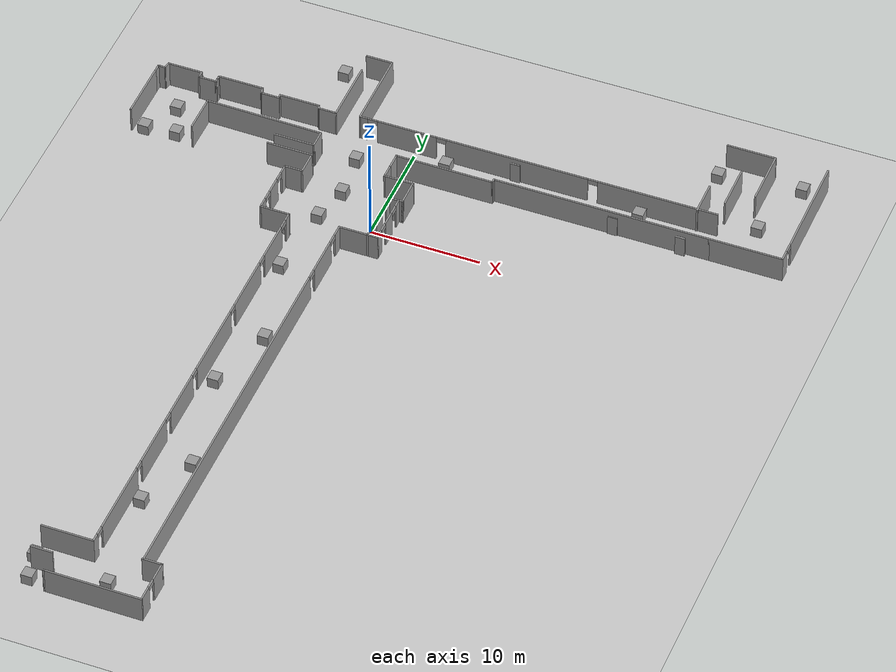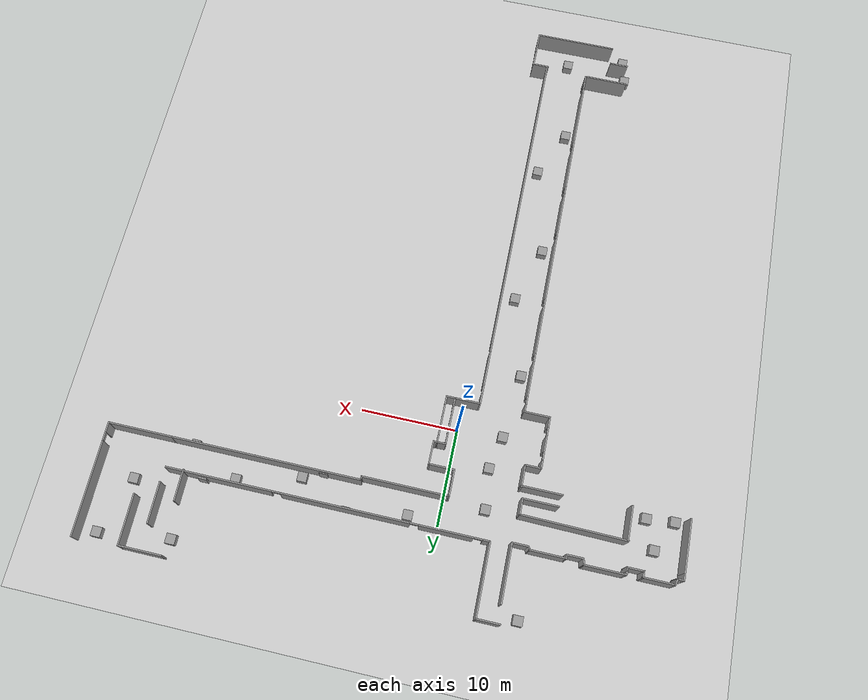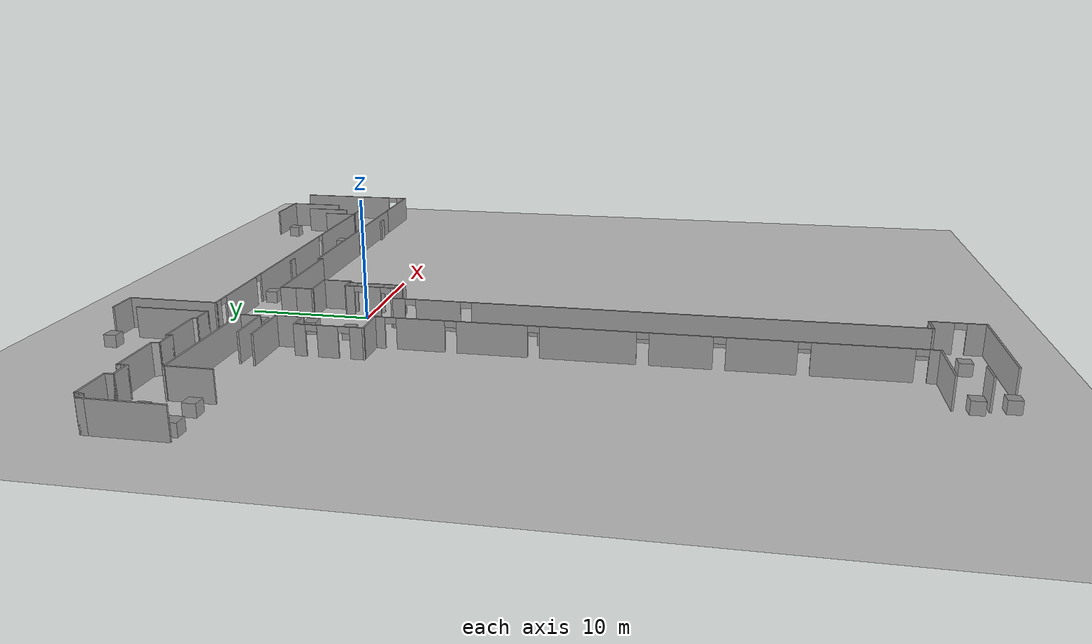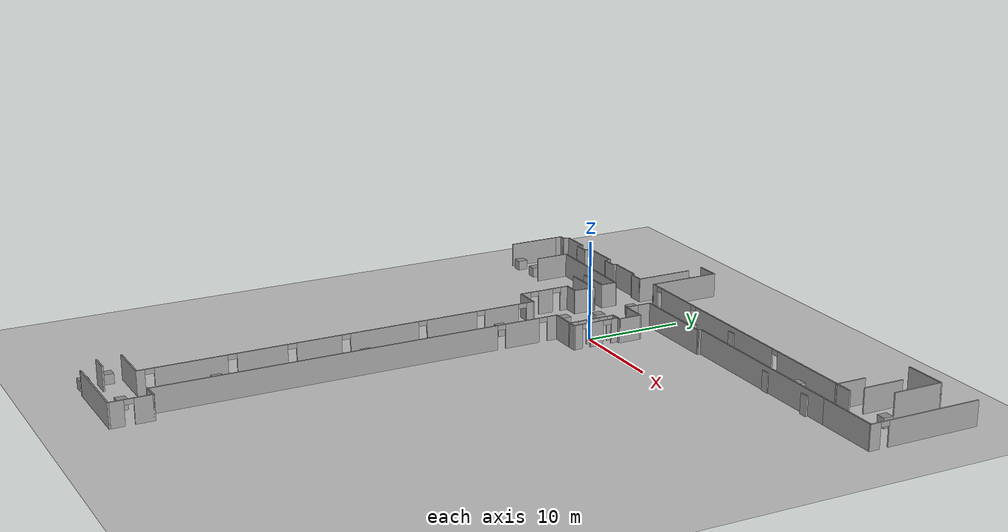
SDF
<sdf version="1.6">
 <world name="default">
  <light name="sun" type="directional">
   <pose>0 0 10 0 -0 0</pose>
   <diffuse>0.8 0.8 0.8 1</diffuse>
   <specular>0.1 0.1 0.1 1</specular>
   <attenuation>
    <range>1000</range>
    <constant>0.9</constant>
    <linear>0.01</linear>
    <quadratic>0.001</quadratic>
   </attenuation>
   <direction>-0.5 0.5 -1</direction>
  </light>
  <model name="ground_plane">
   <static>1</static>
   <link name="link">
    <collision name="collision">
     <geometry><plane><normal>0 0 1</normal><size>100 100</size></plane></geometry>
     <surface><friction><ode><mu>100</mu><mu2>50</mu2></ode></friction></surface>
    </collision>
    <visual name="visual">
     <cast_shadows>0</cast_shadows>
     <geometry><plane><normal>0 0 1</normal><size>100 100</size></plane></geometry>
     <material>
      <script><uri>file://media/materials/scripts/gazebo.material</uri><name>Gazebo/Grey</name></script>
     </material>
    </visual>
   </link>
  </model>
  <gravity>0 0 -9.8</gravity>
  <magnetic_field>6e-06 2.3e-05 -4.2e-05</magnetic_field>
  <atmosphere type="adiabatic"/>
  <physics name="default_physics" default="0" type="ode">
   <max_step_size>0.001</max_step_size>
   <real_time_factor>1</real_time_factor>
   <real_time_update_rate>1000</real_time_update_rate>
  </physics>
  <scene><ambient>0.4 0.4 0.4 1</ambient><background>0.7 0.7 0.7 1</background><shadows>1</shadows></scene>
  <spherical_coordinates>
   <surface_model>EARTH_WGS84</surface_model>
   <latitude_deg>0</latitude_deg>
   <longitude_deg>0</longitude_deg>
   <elevation>0</elevation>
   <heading_deg>0</heading_deg>
  </spherical_coordinates>
  <model name="Untitled">
   <pose>5.24668 -14.5439 0 0 -0 0</pose>
   <link name="Door_21">
    <collision name="Door_21_Collision">
     <geometry><box><size>0.9 0.17 2</size></box></geometry>
     <pose>0 0 1 0 -0 0</pose>
    </collision>
    <visual name="Door_21_Visual">
     <pose>0 0 1 0 -0 0</pose>
     <geometry><box><size>0.9 0.17 2</size></box></geometry>
     <material>
      <script><uri>file://media/materials/scripts/gazebo.material</uri><name>Gazebo/Grey</name></script>
     </material>
    </visual>
    <pose>6.93392 22.1522 0 0 -0 0</pose>
   </link>
   <link name="Door_22">
    <collision name="Door_22_Collision">
     <geometry><box><size>0.9 0.17 2</size></box></geometry>
     <pose>0 0 1 0 -0 0</pose>
    </collision>
    <visual name="Door_22_Visual">
     <pose>0 0 1 0 -0 0</pose>
     <geometry><box><size>0.9 0.17 2</size></box></geometry>
     <material>
      <script><uri>file://media/materials/scripts/gazebo.material</uri><name>Gazebo/Grey</name></script>
     </material>
    </visual>
    <pose>14.0126 21.9752 0 0 -0 0</pose>
   </link>
   <link name="Door_23">
    <collision name="Door_23_Collision">
     <geometry><box><size>0.9 0.17 2</size></box></geometry>
     <pose>0 0 1 0 -0 0</pose>
    </collision>
    <visual name="Door_23_Visual">
     <pose>0 0 1 0 -0 0</pose>
     <geometry><box><size>0.9 0.17 2</size></box></geometry>
     <material>
      <script><uri>file://media/materials/scripts/gazebo.material</uri><name>Gazebo/Grey</name></script>
     </material>
    </visual>
    <pose>20.2065 21.7983 0 0 -0 0</pose>
   </link>
   <link name="Door_25">
    <collision name="Door_25_Collision">
     <geometry><box><size>0.9 0.17 2</size></box></geometry>
     <pose>0 0 1 0 -0 0</pose>
    </collision>
    <visual name="Door_25_Visual">
     <pose>0 0 1 0 -0 0</pose>
     <geometry><box><size>0.9 0.17 2</size></box></geometry>
     <material>
      <script><uri>file://media/materials/scripts/gazebo.material</uri><name>Gazebo/Grey</name></script>
     </material>
    </visual>
    <pose>3.92546 24.9837 0 0 -0 0</pose>
   </link>
   <link name="Door_27">
    <collision name="Door_27_Collision">
     <geometry><box><size>0.9 0.17 2</size></box></geometry>
     <pose>0 0 1 0 -0 0</pose>
    </collision>
    <visual name="Door_27_Visual">
     <pose>0 0 1 0 -0 0</pose>
     <geometry><box><size>0.9 0.17 2</size></box></geometry>
     <material>
      <script><uri>file://media/materials/scripts/gazebo.material</uri><name>Gazebo/Grey</name></script>
     </material>
    </visual>
    <pose>18.6138 25.3376 0 0 -0 0</pose>
   </link>
   <link name="Wall_10">
    <pose>-3.49868 14.2381 0 0 -0 1.5708</pose>
    <visual name="Wall_10_Visual_0">
     <pose>-2.03539 0 1.25 0 -0 0</pose>
     <geometry><box><size>0.929216 0.15 2.5</size></box></geometry>
     <material>
      <script><uri>file://media/materials/scripts/gazebo.material</uri><name>Gazebo/Grey</name></script>
      <ambient>1 1 1 1</ambient>
     </material>
    </visual>
    <collision name="Wall_10_Collision_0">
     <geometry><box><size>0.929216 0.15 2.5</size></box></geometry>
     <pose>-2.03539 0 1.25 0 -0 0</pose>
    </collision>
    <visual name="Wall_10_Visual_1">
     <pose>0.040984 0 1.25 0 -0 0</pose>
     <geometry><box><size>1.42354 0.15 2.5</size></box></geometry>
     <material>
      <script><uri>file://media/materials/scripts/gazebo.material</uri><name>Gazebo/Grey</name></script>
      <ambient>1 1 1 1</ambient>
     </material>
    </visual>
    <collision name="Wall_10_Collision_1">
     <geometry><box><size>1.42354 0.15 2.5</size></box></geometry>
     <pose>0.040984 0 1.25 0 -0 0</pose>
    </collision>
    <visual name="Wall_10_Visual_2">
     <pose>2.07638 0 1.25 0 -0 0</pose>
     <geometry><box><size>0.847248 0.15 2.5</size></box></geometry>
     <material>
      <script><uri>file://media/materials/scripts/gazebo.material</uri><name>Gazebo/Grey</name></script>
      <ambient>1 1 1 1</ambient>
     </material>
    </visual>
    <collision name="Wall_10_Collision_2">
     <geometry><box><size>0.847248 0.15 2.5</size></box></geometry>
     <pose>2.07638 0 1.25 0 -0 0</pose>
    </collision>
    <visual name="Wall_10_Visual_3">
     <pose>-1.12078 0 2.25 0 -0 0</pose>
     <geometry><box><size>0.9 0.15 0.5</size></box></geometry>
     <material>
      <script><uri>file://media/materials/scripts/gazebo.material</uri><name>Gazebo/Grey</name></script>
      <ambient>1 1 1 1</ambient>
     </material>
    </visual>
    <collision name="Wall_10_Collision_3">
     <geometry><box><size>0.9 0.15 0.5</size></box></geometry>
     <pose>-1.12078 0 2.25 0 -0 0</pose>
    </collision>
    <visual name="Wall_10_Visual_4">
     <pose>1.20275 0 2.25 0 -0 0</pose>
     <geometry><box><size>0.9 0.15 0.5</size></box></geometry>
     <material>
      <script><uri>file://media/materials/scripts/gazebo.material</uri><name>Gazebo/Grey</name></script>
      <ambient>1 1 1 1</ambient>
     </material>
    </visual>
    <collision name="Wall_10_Collision_4">
     <geometry><box><size>0.9 0.15 0.5</size></box></geometry>
     <pose>1.20275 0 2.25 0 -0 0</pose>
    </collision>
   </link>
   <link name="Wall_13">
    <collision name="Wall_13_Collision">
     <geometry><box><size>1.02654 0.15 2.5</size></box></geometry>
     <pose>0 0 1.25 0 -0 0</pose>
    </collision>
    <visual name="Wall_13_Visual">
     <pose>0 0 1.25 0 -0 0</pose>
     <geometry><box><size>1.02654 0.15 2.5</size></box></geometry>
     <material>
      <script><uri>file://media/materials/scripts/gazebo.material</uri><name>Gazebo/Grey</name></script>
      <ambient>1 1 1 1</ambient>
     </material>
    </visual>
    <pose>-3.93676 16.65 0 0 -0 0.02984</pose>
   </link>
   <link name="Wall_16">
    <collision name="Wall_16_Collision">
     <geometry><box><size>2.75 0.15 2.5</size></box></geometry>
     <pose>0 0 1.25 0 -0 0</pose>
    </collision>
    <visual name="Wall_16_Visual">
     <pose>0 0 1.25 0 -0 0</pose>
     <geometry><box><size>2.75 0.15 2.5</size></box></geometry>
     <material>
      <script><uri>file://media/materials/scripts/gazebo.material</uri><name>Gazebo/Grey</name></script>
      <ambient>1 1 1 1</ambient>
     </material>
    </visual>
    <pose>-5.67483 11.7869 0 0 -0 3.14159</pose>
   </link>
   <link name="Wall_18">
    <pose>-6.97484 -8.84982 0 0 0 -1.5708</pose>
    <visual name="Wall_18_Visual_0">
     <pose>-20.12 0 1.25 0 -0 0</pose>
     <geometry><box><size>1.18354 0.15 2.5</size></box></geometry>
     <material>
      <script><uri>file://media/materials/scripts/gazebo.material</uri><name>Gazebo/Grey</name></script>
      <ambient>1 1 1 1</ambient>
     </material>
    </visual>
    <collision name="Wall_18_Collision_0">
     <geometry><box><size>1.18354 0.15 2.5</size></box></geometry>
     <pose>-20.12 0 1.25 0 -0 0</pose>
    </collision>
    <visual name="Wall_18_Visual_1">
     <pose>-16.7893 0 1.25 0 -0 0</pose>
     <geometry><box><size>3.67779 0.15 2.5</size></box></geometry>
     <material>
      <script><uri>file://media/materials/scripts/gazebo.material</uri><name>Gazebo/Grey</name></script>
      <ambient>1 1 1 1</ambient>
     </material>
    </visual>
    <collision name="Wall_18_Collision_1">
     <geometry><box><size>3.67779 0.15 2.5</size></box></geometry>
     <pose>-16.7893 0 1.25 0 -0 0</pose>
    </collision>
    <visual name="Wall_18_Visual_2">
     <pose>3.33067 0 1.25 0 -0 0</pose>
     <geometry><box><size>34.7622 0.15 2.5</size></box></geometry>
     <material>
      <script><uri>file://media/materials/scripts/gazebo.material</uri><name>Gazebo/Grey</name></script>
      <ambient>1 1 1 1</ambient>
     </material>
    </visual>
    <collision name="Wall_18_Collision_2">
     <geometry><box><size>34.7622 0.15 2.5</size></box></geometry>
     <pose>3.33067 0 1.25 0 -0 0</pose>
    </collision>
    <visual name="Wall_18_Visual_3">
     <pose>-19.0782 0 2.25 0 -0 0</pose>
     <geometry><box><size>0.9 0.15 0.5</size></box></geometry>
     <material>
      <script><uri>file://media/materials/scripts/gazebo.material</uri><name>Gazebo/Grey</name></script>
      <ambient>1 1 1 1</ambient>
     </material>
    </visual>
    <collision name="Wall_18_Collision_3">
     <geometry><box><size>0.9 0.15 0.5</size></box></geometry>
     <pose>-19.0782 0 2.25 0 -0 0</pose>
    </collision>
    <visual name="Wall_18_Visual_4">
     <pose>-14.5004 0 2.25 0 -0 0</pose>
     <geometry><box><size>0.9 0.15 0.5</size></box></geometry>
     <material>
      <script><uri>file://media/materials/scripts/gazebo.material</uri><name>Gazebo/Grey</name></script>
      <ambient>1 1 1 1</ambient>
     </material>
    </visual>
    <collision name="Wall_18_Collision_4">
     <geometry><box><size>0.9 0.15 0.5</size></box></geometry>
     <pose>-14.5004 0 2.25 0 -0 0</pose>
    </collision>
   </link>
   <link name="Wall_19">
    <collision name="Wall_19_Collision">
     <geometry><box><size>1.82651 0.15 2.5</size></box></geometry>
     <pose>0 0 1.25 0 -0 0</pose>
    </collision>
    <visual name="Wall_19_Visual">
     <pose>0 0 1.25 0 -0 0</pose>
     <geometry><box><size>1.82651 0.15 2.5</size></box></geometry>
     <material>
      <script><uri>file://media/materials/scripts/gazebo.material</uri><name>Gazebo/Grey</name></script>
      <ambient>1 1 1 1</ambient>
     </material>
    </visual>
    <pose>-6.21309 -29.5631 0 0 -0 0</pose>
   </link>
   <link name="Wall_20">
    <pose>-5.37484 -31.6131 0 0 0 -1.5708</pose>
    <visual name="Wall_20_Visual_0">
     <pose>-1.19221 0 1.25 0 -0 0</pose>
     <geometry><box><size>1.86558 0.15 2.5</size></box></geometry>
     <material>
      <script><uri>file://media/materials/scripts/gazebo.material</uri><name>Gazebo/Grey</name></script>
      <ambient>1 1 1 1</ambient>
     </material>
    </visual>
    <collision name="Wall_20_Collision_0">
     <geometry><box><size>1.86558 0.15 2.5</size></box></geometry>
     <pose>-1.19221 0 1.25 0 -0 0</pose>
    </collision>
    <visual name="Wall_20_Visual_1">
     <pose>1.38279 0 1.25 0 -0 0</pose>
     <geometry><box><size>1.48442 0.15 2.5</size></box></geometry>
     <material>
      <script><uri>file://media/materials/scripts/gazebo.material</uri><name>Gazebo/Grey</name></script>
      <ambient>1 1 1 1</ambient>
     </material>
    </visual>
    <collision name="Wall_20_Collision_1">
     <geometry><box><size>1.48442 0.15 2.5</size></box></geometry>
     <pose>1.38279 0 1.25 0 -0 0</pose>
    </collision>
    <visual name="Wall_20_Visual_2">
     <pose>0.190582 0 2.25 0 -0 0</pose>
     <geometry><box><size>0.9 0.15 0.5</size></box></geometry>
     <material>
      <script><uri>file://media/materials/scripts/gazebo.material</uri><name>Gazebo/Grey</name></script>
      <ambient>1 1 1 1</ambient>
     </material>
    </visual>
    <collision name="Wall_20_Collision_2">
     <geometry><box><size>0.9 0.15 0.5</size></box></geometry>
     <pose>0.190582 0 2.25 0 -0 0</pose>
    </collision>
   </link>
   <link name="Wall_21">
    <collision name="Wall_21_Collision">
     <geometry><box><size>8.75 0.15 2.5</size></box></geometry>
     <pose>0 0 1.25 0 -0 0</pose>
    </collision>
    <visual name="Wall_21_Visual">
     <pose>0 0 1.25 0 -0 0</pose>
     <geometry><box><size>8.75 0.15 2.5</size></box></geometry>
     <material>
      <script><uri>file://media/materials/scripts/gazebo.material</uri><name>Gazebo/Grey</name></script>
      <ambient>1 1 1 1</ambient>
     </material>
    </visual>
    <pose>-9.67484 -33.6631 0 0 -0 3.14159</pose>
   </link>
   <link name="Wall_22">
    <collision name="Wall_22_Collision">
     <geometry><box><size>0.16 0.15 2.5</size></box></geometry>
     <pose>0 0 1.25 0 -0 0</pose>
    </collision>
    <visual name="Wall_22_Visual">
     <pose>0 0 1.25 0 -0 0</pose>
     <geometry><box><size>0.16 0.15 2.5</size></box></geometry>
     <material>
      <script><uri>file://media/materials/scripts/gazebo.material</uri><name>Gazebo/Grey</name></script>
      <ambient>1 1 1 1</ambient>
     </material>
    </visual>
    <pose>-13.9698 -33.6631 0 0 -0 0</pose>
   </link>
   <link name="Wall_24">
    <collision name="Wall_24_Collision">
     <geometry><box><size>0.5 0.15 2.5</size></box></geometry>
     <pose>0 0 1.25 0 -0 0</pose>
    </collision>
    <visual name="Wall_24_Visual">
     <pose>0 0 1.25 0 -0 0</pose>
     <geometry><box><size>0.5 0.15 2.5</size></box></geometry>
     <material>
      <script><uri>file://media/materials/scripts/gazebo.material</uri><name>Gazebo/Grey</name></script>
      <ambient>1 1 1 1</ambient>
     </material>
    </visual>
    <pose>-3.32368 16.6631 0 0 -0 0</pose>
   </link>
   <link name="Wall_25">
    <collision name="Wall_25_Collision">
     <geometry><box><size>2.5 0.15 2.5</size></box></geometry>
     <pose>0 0 1.25 0 -0 0</pose>
    </collision>
    <visual name="Wall_25_Visual">
     <pose>0 0 1.25 0 -0 0</pose>
     <geometry><box><size>2.5 0.15 2.5</size></box></geometry>
     <material>
      <script><uri>file://media/materials/scripts/gazebo.material</uri><name>Gazebo/Grey</name></script>
      <ambient>1 1 1 1</ambient>
     </material>
    </visual>
    <pose>-3.14868 17.8381 0 0 -0 1.5708</pose>
   </link>
   <link name="Wall_26">
    <collision name="Wall_26_Collision">
     <geometry><box><size>2.75 0.15 2.5</size></box></geometry>
     <pose>0 0 1.25 0 -0 0</pose>
    </collision>
    <visual name="Wall_26_Visual">
     <pose>0 0 1.25 0 -0 0</pose>
     <geometry><box><size>2.75 0.15 2.5</size></box></geometry>
     <material>
      <script><uri>file://media/materials/scripts/gazebo.material</uri><name>Gazebo/Grey</name></script>
      <ambient>1 1 1 1</ambient>
     </material>
    </visual>
    <pose>-4.44868 19.0131 0 0 -0 3.14159</pose>
   </link>
   <link name="Wall_27">
    <collision name="Wall_27_Collision">
     <geometry><box><size>1.5 0.15 2.5</size></box></geometry>
     <pose>0 0 1.25 0 -0 0</pose>
    </collision>
    <visual name="Wall_27_Visual">
     <pose>0 0 1.25 0 -0 0</pose>
     <geometry><box><size>1.5 0.15 2.5</size></box></geometry>
     <material>
      <script><uri>file://media/materials/scripts/gazebo.material</uri><name>Gazebo/Grey</name></script>
      <ambient>1 1 1 1</ambient>
     </material>
    </visual>
    <pose>-5.74868 19.6881 0 0 -0 1.5708</pose>
   </link>
   <link name="Wall_28">
    <collision name="Wall_28_Collision">
     <geometry><box><size>1.5 0.15 2.5</size></box></geometry>
     <pose>0 0 1.25 0 -0 0</pose>
    </collision>
    <visual name="Wall_28_Visual">
     <pose>0 0 1.25 0 -0 0</pose>
     <geometry><box><size>1.5 0.15 2.5</size></box></geometry>
     <material>
      <script><uri>file://media/materials/scripts/gazebo.material</uri><name>Gazebo/Grey</name></script>
      <ambient>1 1 1 1</ambient>
     </material>
    </visual>
    <pose>-5.74868 21.0381 0 0 -0 1.5708</pose>
   </link>
   <link name="Wall_29">
    <collision name="Wall_29_Collision">
     <geometry><box><size>9 0.15 2.5</size></box></geometry>
     <pose>0 0 1.25 0 -0 0</pose>
    </collision>
    <visual name="Wall_29_Visual">
     <pose>0 0 1.25 0 -0 0</pose>
     <geometry><box><size>9 0.15 2.5</size></box></geometry>
     <material>
      <script><uri>file://media/materials/scripts/gazebo.material</uri><name>Gazebo/Grey</name></script>
      <ambient>1 1 1 1</ambient>
     </material>
    </visual>
    <pose>-1.32368 21.7131 0 0 -0 0</pose>
   </link>
   <link name="Wall_30">
    <collision name="Wall_30_Collision">
     <geometry><box><size>0.5 0.15 2.5</size></box></geometry>
     <pose>0 0 1.25 0 -0 0</pose>
    </collision>
    <visual name="Wall_30_Visual">
     <pose>0 0 1.25 0 -0 0</pose>
     <geometry><box><size>0.5 0.15 2.5</size></box></geometry>
     <material>
      <script><uri>file://media/materials/scripts/gazebo.material</uri><name>Gazebo/Grey</name></script>
      <ambient>1 1 1 1</ambient>
     </material>
    </visual>
    <pose>3.10132 21.8881 0 0 -0 1.5708</pose>
   </link>
   <link name="Wall_31">
    <collision name="Wall_31_Collision">
     <geometry><box><size>19.75 0.15 2.5</size></box></geometry>
     <pose>0 0 1.25 0 -0 0</pose>
    </collision>
    <visual name="Wall_31_Visual">
     <pose>0 0 1.25 0 -0 0</pose>
     <geometry><box><size>19.75 0.15 2.5</size></box></geometry>
     <material>
      <script><uri>file://media/materials/scripts/gazebo.material</uri><name>Gazebo/Grey</name></script>
      <ambient>1 1 1 1</ambient>
     </material>
    </visual>
    <pose>12.9013 22.0631 0 0 -0 0</pose>
   </link>
   <link name="Wall_33">
    <pose>-11.5526 -8.79923 0 0 -0 1.5708</pose>
    <visual name="Wall_33_Visual_0">
     <pose>-20.0811 0 1.25 0 -0 0</pose>
     <geometry><box><size>0.837718 0.15 2.5</size></box></geometry>
     <material>
      <script><uri>file://media/materials/scripts/gazebo.material</uri><name>Gazebo/Grey</name></script>
      <ambient>1 1 1 1</ambient>
     </material>
    </visual>
    <collision name="Wall_33_Collision_0">
     <geometry><box><size>0.837718 0.15 2.5</size></box></geometry>
     <pose>-20.0811 0 1.25 0 -0 0</pose>
    </collision>
    <visual name="Wall_33_Visual_1">
     <pose>-15.2438 0 1.25 0 -0 0</pose>
     <geometry><box><size>7.03702 0.15 2.5</size></box></geometry>
     <material>
      <script><uri>file://media/materials/scripts/gazebo.material</uri><name>Gazebo/Grey</name></script>
      <ambient>1 1 1 1</ambient>
     </material>
    </visual>
    <collision name="Wall_33_Collision_1">
     <geometry><box><size>7.03702 0.15 2.5</size></box></geometry>
     <pose>-15.2438 0 1.25 0 -0 0</pose>
    </collision>
    <visual name="Wall_33_Visual_2">
     <pose>-8.32432 0 1.25 0 -0 0</pose>
     <geometry><box><size>5.00188 0.15 2.5</size></box></geometry>
     <material>
      <script><uri>file://media/materials/scripts/gazebo.material</uri><name>Gazebo/Grey</name></script>
      <ambient>1 1 1 1</ambient>
     </material>
    </visual>
    <collision name="Wall_33_Collision_2">
     <geometry><box><size>5.00188 0.15 2.5</size></box></geometry>
     <pose>-8.32432 0 1.25 0 -0 0</pose>
    </collision>
    <visual name="Wall_33_Visual_3">
     <pose>-2.62595 0 1.25 0 -0 0</pose>
     <geometry><box><size>4.59486 0.15 2.5</size></box></geometry>
     <material>
      <script><uri>file://media/materials/scripts/gazebo.material</uri><name>Gazebo/Grey</name></script>
      <ambient>1 1 1 1</ambient>
     </material>
    </visual>
    <collision name="Wall_33_Collision_3">
     <geometry><box><size>4.59486 0.15 2.5</size></box></geometry>
     <pose>-2.62595 0 1.25 0 -0 0</pose>
    </collision>
    <visual name="Wall_33_Visual_4">
     <pose>4.15299 0 1.25 0 -0 0</pose>
     <geometry><box><size>7.16302 0.15 2.5</size></box></geometry>
     <material>
      <script><uri>file://media/materials/scripts/gazebo.material</uri><name>Gazebo/Grey</name></script>
      <ambient>1 1 1 1</ambient>
     </material>
    </visual>
    <collision name="Wall_33_Collision_4">
     <geometry><box><size>7.16302 0.15 2.5</size></box></geometry>
     <pose>4.15299 0 1.25 0 -0 0</pose>
    </collision>
    <visual name="Wall_33_Visual_5">
     <pose>11.3423 0 1.25 0 -0 0</pose>
     <geometry><box><size>5.41564 0.15 2.5</size></box></geometry>
     <material>
      <script><uri>file://media/materials/scripts/gazebo.material</uri><name>Gazebo/Grey</name></script>
      <ambient>1 1 1 1</ambient>
     </material>
    </visual>
    <collision name="Wall_33_Collision_5">
     <geometry><box><size>5.41564 0.15 2.5</size></box></geometry>
     <pose>11.3423 0 1.25 0 -0 0</pose>
    </collision>
    <visual name="Wall_33_Visual_6">
     <pose>16.8387 0 1.25 0 -0 0</pose>
     <geometry><box><size>3.77715 0.15 2.5</size></box></geometry>
     <material>
      <script><uri>file://media/materials/scripts/gazebo.material</uri><name>Gazebo/Grey</name></script>
      <ambient>1 1 1 1</ambient>
     </material>
    </visual>
    <collision name="Wall_33_Collision_6">
     <geometry><box><size>3.77715 0.15 2.5</size></box></geometry>
     <pose>16.8387 0 1.25 0 -0 0</pose>
    </collision>
    <visual name="Wall_33_Visual_7">
     <pose>20.0636 0 1.25 0 -0 0</pose>
     <geometry><box><size>0.872717 0.15 2.5</size></box></geometry>
     <material>
      <script><uri>file://media/materials/scripts/gazebo.material</uri><name>Gazebo/Grey</name></script>
      <ambient>1 1 1 1</ambient>
     </material>
    </visual>
    <collision name="Wall_33_Collision_7">
     <geometry><box><size>0.872717 0.15 2.5</size></box></geometry>
     <pose>20.0636 0 1.25 0 -0 0</pose>
    </collision>
    <visual name="Wall_33_Visual_8">
     <pose>-19.2123 0 2.25 0 -0 0</pose>
     <geometry><box><size>0.9 0.15 0.5</size></box></geometry>
     <material>
      <script><uri>file://media/materials/scripts/gazebo.material</uri><name>Gazebo/Grey</name></script>
      <ambient>1 1 1 1</ambient>
     </material>
    </visual>
    <collision name="Wall_33_Collision_8">
     <geometry><box><size>0.9 0.15 0.5</size></box></geometry>
     <pose>-19.2123 0 2.25 0 -0 0</pose>
    </collision>
    <visual name="Wall_33_Visual_9">
     <pose>-11.2753 0 2.25 0 -0 0</pose>
     <geometry><box><size>0.9 0.15 0.5</size></box></geometry>
     <material>
      <script><uri>file://media/materials/scripts/gazebo.material</uri><name>Gazebo/Grey</name></script>
      <ambient>1 1 1 1</ambient>
     </material>
    </visual>
    <collision name="Wall_33_Collision_9">
     <geometry><box><size>0.9 0.15 0.5</size></box></geometry>
     <pose>-11.2753 0 2.25 0 -0 0</pose>
    </collision>
    <visual name="Wall_33_Visual_10">
     <pose>-5.37338 0 2.25 0 -0 0</pose>
     <geometry><box><size>0.9 0.15 0.5</size></box></geometry>
     <material>
      <script><uri>file://media/materials/scripts/gazebo.material</uri><name>Gazebo/Grey</name></script>
      <ambient>1 1 1 1</ambient>
     </material>
    </visual>
    <collision name="Wall_33_Collision_10">
     <geometry><box><size>0.9 0.15 0.5</size></box></geometry>
     <pose>-5.37338 0 2.25 0 -0 0</pose>
    </collision>
    <visual name="Wall_33_Visual_11">
     <pose>0.121477 0 2.25 0 -0 0</pose>
     <geometry><box><size>0.9 0.15 0.5</size></box></geometry>
     <material>
      <script><uri>file://media/materials/scripts/gazebo.material</uri><name>Gazebo/Grey</name></script>
      <ambient>1 1 1 1</ambient>
     </material>
    </visual>
    <collision name="Wall_33_Collision_11">
     <geometry><box><size>0.9 0.15 0.5</size></box></geometry>
     <pose>0.121477 0 2.25 0 -0 0</pose>
    </collision>
    <visual name="Wall_33_Visual_12">
     <pose>8.18449 0 2.25 0 -0 0</pose>
     <geometry><box><size>0.9 0.15 0.5</size></box></geometry>
     <material>
      <script><uri>file://media/materials/scripts/gazebo.material</uri><name>Gazebo/Grey</name></script>
      <ambient>1 1 1 1</ambient>
     </material>
    </visual>
    <collision name="Wall_33_Collision_12">
     <geometry><box><size>0.9 0.15 0.5</size></box></geometry>
     <pose>8.18449 0 2.25 0 -0 0</pose>
    </collision>
    <visual name="Wall_33_Visual_13">
     <pose>14.5001 0 2.25 0 -0 0</pose>
     <geometry><box><size>0.9 0.15 0.5</size></box></geometry>
     <material>
      <script><uri>file://media/materials/scripts/gazebo.material</uri><name>Gazebo/Grey</name></script>
      <ambient>1 1 1 1</ambient>
     </material>
    </visual>
    <collision name="Wall_33_Collision_13">
     <geometry><box><size>0.9 0.15 0.5</size></box></geometry>
     <pose>14.5001 0 2.25 0 -0 0</pose>
    </collision>
    <visual name="Wall_33_Visual_14">
     <pose>19.1773 0 2.25 0 -0 0</pose>
     <geometry><box><size>0.9 0.15 0.5</size></box></geometry>
     <material>
      <script><uri>file://media/materials/scripts/gazebo.material</uri><name>Gazebo/Grey</name></script>
      <ambient>1 1 1 1</ambient>
     </material>
    </visual>
    <collision name="Wall_33_Collision_14">
     <geometry><box><size>0.9 0.15 0.5</size></box></geometry>
     <pose>19.1773 0 2.25 0 -0 0</pose>
    </collision>
   </link>
   <link name="Wall_34">
    <collision name="Wall_34_Collision">
     <geometry><box><size>2.75 0.15 2.5</size></box></geometry>
     <pose>0 0 1.25 0 -0 0</pose>
    </collision>
    <visual name="Wall_34_Visual">
     <pose>0 0 1.25 0 -0 0</pose>
     <geometry><box><size>2.75 0.15 2.5</size></box></geometry>
     <material>
      <script><uri>file://media/materials/scripts/gazebo.material</uri><name>Gazebo/Grey</name></script>
      <ambient>1 1 1 1</ambient>
     </material>
    </visual>
    <pose>-12.8526 11.6258 0 0 -0 3.14159</pose>
   </link>
   <link name="Wall_35">
    <pose>-14.1526 14.3008 0 0 -0 1.5708</pose>
    <visual name="Wall_35_Visual_0">
     <pose>-2.18556 0 1.25 0 -0 0</pose>
     <geometry><box><size>1.12888 0.15 2.5</size></box></geometry>
     <material>
      <script><uri>file://media/materials/scripts/gazebo.material</uri><name>Gazebo/Grey</name></script>
      <ambient>1 1 1 1</ambient>
     </material>
    </visual>
    <collision name="Wall_35_Collision_0">
     <geometry><box><size>1.12888 0.15 2.5</size></box></geometry>
     <pose>-2.18556 0 1.25 0 -0 0</pose>
    </collision>
    <visual name="Wall_35_Visual_1">
     <pose>0.09366 0 1.25 0 -0 0</pose>
     <geometry><box><size>1.62955 0.15 2.5</size></box></geometry>
     <material>
      <script><uri>file://media/materials/scripts/gazebo.material</uri><name>Gazebo/Grey</name></script>
      <ambient>1 1 1 1</ambient>
     </material>
    </visual>
    <collision name="Wall_35_Collision_1">
     <geometry><box><size>1.62955 0.15 2.5</size></box></geometry>
     <pose>0.09366 0 1.25 0 -0 0</pose>
    </collision>
    <visual name="Wall_35_Visual_2">
     <pose>2.27922 0 1.25 0 -0 0</pose>
     <geometry><box><size>0.941564 0.15 2.5</size></box></geometry>
     <material>
      <script><uri>file://media/materials/scripts/gazebo.material</uri><name>Gazebo/Grey</name></script>
      <ambient>1 1 1 1</ambient>
     </material>
    </visual>
    <collision name="Wall_35_Collision_2">
     <geometry><box><size>0.941564 0.15 2.5</size></box></geometry>
     <pose>2.27922 0 1.25 0 -0 0</pose>
    </collision>
    <visual name="Wall_35_Visual_3">
     <pose>-1.17112 0 2.25 0 -0 0</pose>
     <geometry><box><size>0.9 0.15 0.5</size></box></geometry>
     <material>
      <script><uri>file://media/materials/scripts/gazebo.material</uri><name>Gazebo/Grey</name></script>
      <ambient>1 1 1 1</ambient>
     </material>
    </visual>
    <collision name="Wall_35_Collision_3">
     <geometry><box><size>0.9 0.15 0.5</size></box></geometry>
     <pose>-1.17112 0 2.25 0 -0 0</pose>
    </collision>
    <visual name="Wall_35_Visual_4">
     <pose>1.35844 0 2.25 0 -0 0</pose>
     <geometry><box><size>0.9 0.15 0.5</size></box></geometry>
     <material>
      <script><uri>file://media/materials/scripts/gazebo.material</uri><name>Gazebo/Grey</name></script>
      <ambient>1 1 1 1</ambient>
     </material>
    </visual>
    <collision name="Wall_35_Collision_4">
     <geometry><box><size>0.9 0.15 0.5</size></box></geometry>
     <pose>1.35844 0 2.25 0 -0 0</pose>
    </collision>
   </link>
   <link name="Wall_36">
    <collision name="Wall_36_Collision">
     <geometry><box><size>1.75 0.15 2.5</size></box></geometry>
     <pose>0 0 1.25 0 -0 0</pose>
    </collision>
    <visual name="Wall_36_Visual">
     <pose>0 0 1.25 0 -0 0</pose>
     <geometry><box><size>1.75 0.15 2.5</size></box></geometry>
     <material>
      <script><uri>file://media/materials/scripts/gazebo.material</uri><name>Gazebo/Grey</name></script>
      <ambient>1 1 1 1</ambient>
     </material>
    </visual>
    <pose>-13.3526 16.9758 0 0 -0 0</pose>
   </link>
   <link name="Wall_37">
    <collision name="Wall_37_Collision">
     <geometry><box><size>2.36206 0.15 2.5</size></box></geometry>
     <pose>0 0 1.25 0 -0 0</pose>
    </collision>
    <visual name="Wall_37_Visual">
     <pose>0 0 1.25 0 -0 0</pose>
     <geometry><box><size>2.36206 0.15 2.5</size></box></geometry>
     <material>
      <script><uri>file://media/materials/scripts/gazebo.material</uri><name>Gazebo/Grey</name></script>
      <ambient>1 1 1 1</ambient>
     </material>
    </visual>
    <pose>-12.5526 18.0818 0 0 -0 1.5708</pose>
   </link>
   <link name="Wall_38">
    <collision name="Wall_38_Collision">
     <geometry><box><size>4.25 0.15 2.5</size></box></geometry>
     <pose>0 0 1.25 0 -0 0</pose>
    </collision>
    <visual name="Wall_38_Visual">
     <pose>0 0 1.25 0 -0 0</pose>
     <geometry><box><size>4.25 0.15 2.5</size></box></geometry>
     <material>
      <script><uri>file://media/materials/scripts/gazebo.material</uri><name>Gazebo/Grey</name></script>
      <ambient>1 1 1 1</ambient>
     </material>
    </visual>
    <pose>-14.6026 19.1113 0 0 -0 3.14159</pose>
   </link>
   <link name="Wall_40">
    <collision name="Wall_40_Collision">
     <geometry><box><size>3.75 0.15 2.5</size></box></geometry>
     <pose>0 0 1.25 0 -0 0</pose>
    </collision>
    <visual name="Wall_40_Visual">
     <pose>0 0 1.25 0 -0 0</pose>
     <geometry><box><size>3.75 0.15 2.5</size></box></geometry>
     <material>
      <script><uri>file://media/materials/scripts/gazebo.material</uri><name>Gazebo/Grey</name></script>
      <ambient>1 1 1 1</ambient>
     </material>
    </visual>
    <pose>-14.6677 20.3132 0 0 -0 0</pose>
   </link>
   <link name="Wall_41">
    <collision name="Wall_41_Collision">
     <geometry><box><size>1.75 0.15 2.5</size></box></geometry>
     <pose>0 0 1.25 0 -0 0</pose>
    </collision>
    <visual name="Wall_41_Visual">
     <pose>0 0 1.25 0 -0 0</pose>
     <geometry><box><size>1.75 0.15 2.5</size></box></geometry>
     <material>
      <script><uri>file://media/materials/scripts/gazebo.material</uri><name>Gazebo/Grey</name></script>
      <ambient>1 1 1 1</ambient>
     </material>
    </visual>
    <pose>-12.8677 21.1132 0 0 -0 1.5708</pose>
   </link>
   <link name="Wall_42">
    <collision name="Wall_42_Collision">
     <geometry><box><size>10.9041 0.15 2.5</size></box></geometry>
     <pose>0 0 1.25 0 -0 0</pose>
    </collision>
    <visual name="Wall_42_Visual">
     <pose>0 0 1.25 0 -0 0</pose>
     <geometry><box><size>10.9041 0.15 2.5</size></box></geometry>
     <material>
      <script><uri>file://media/materials/scripts/gazebo.material</uri><name>Gazebo/Grey</name></script>
      <ambient>1 1 1 1</ambient>
     </material>
    </visual>
    <pose>-18.2442 21.9897 0 0 -0 3.12736</pose>
   </link>
   <link name="Wall_43">
    <collision name="Wall_43_Collision">
     <geometry><box><size>3.5 0.15 2.5</size></box></geometry>
     <pose>0 0 1.25 0 -0 0</pose>
    </collision>
    <visual name="Wall_43_Visual">
     <pose>0 0 1.25 0 -0 0</pose>
     <geometry><box><size>3.5 0.15 2.5</size></box></geometry>
     <material>
      <script><uri>file://media/materials/scripts/gazebo.material</uri><name>Gazebo/Grey</name></script>
      <ambient>1 1 1 1</ambient>
     </material>
    </visual>
    <pose>-23.5442 20.3147 0 0 0 -1.5708</pose>
   </link>
   <link name="Wall_45">
    <collision name="Wall_45_Collision">
     <geometry><box><size>5.5 0.15 2.5</size></box></geometry>
     <pose>0 0 1.25 0 -0 0</pose>
    </collision>
    <visual name="Wall_45_Visual">
     <pose>0 0 1.25 0 -0 0</pose>
     <geometry><box><size>5.5 0.15 2.5</size></box></geometry>
     <material>
      <script><uri>file://media/materials/scripts/gazebo.material</uri><name>Gazebo/Grey</name></script>
      <ambient>1 1 1 1</ambient>
     </material>
    </visual>
    <pose>-29.3013 21.3237 0 0 -0 1.5708</pose>
   </link>
   <link name="Wall_46">
    <collision name="Wall_46_Collision">
     <geometry><box><size>0.75 0.15 2.5</size></box></geometry>
     <pose>0 0 1.25 0 -0 0</pose>
    </collision>
    <visual name="Wall_46_Visual">
     <pose>0 0 1.25 0 -0 0</pose>
     <geometry><box><size>0.75 0.15 2.5</size></box></geometry>
     <material>
      <script><uri>file://media/materials/scripts/gazebo.material</uri><name>Gazebo/Grey</name></script>
      <ambient>1 1 1 1</ambient>
     </material>
    </visual>
    <pose>-29.3013 24.2987 0 0 -0 1.5708</pose>
   </link>
   <link name="Wall_47">
    <collision name="Wall_47_Collision">
     <geometry><box><size>0.75 0.15 2.5</size></box></geometry>
     <pose>0 0 1.25 0 -0 0</pose>
    </collision>
    <visual name="Wall_47_Visual">
     <pose>0 0 1.25 0 -0 0</pose>
     <geometry><box><size>0.75 0.15 2.5</size></box></geometry>
     <material>
      <script><uri>file://media/materials/scripts/gazebo.material</uri><name>Gazebo/Grey</name></script>
      <ambient>1 1 1 1</ambient>
     </material>
    </visual>
    <pose>-29.0013 24.5987 0 0 -0 0</pose>
   </link>
   <link name="Wall_48">
    <collision name="Wall_48_Collision">
     <geometry><box><size>0.75 0.15 2.5</size></box></geometry>
     <pose>0 0 1.25 0 -0 0</pose>
    </collision>
    <visual name="Wall_48_Visual">
     <pose>0 0 1.25 0 -0 0</pose>
     <geometry><box><size>0.75 0.15 2.5</size></box></geometry>
     <material>
      <script><uri>file://media/materials/scripts/gazebo.material</uri><name>Gazebo/Grey</name></script>
      <ambient>1 1 1 1</ambient>
     </material>
    </visual>
    <pose>-28.6237 24.8885 0 0 -0 1.309</pose>
   </link>
   <link name="Wall_49">
    <collision name="Wall_49_Collision">
     <geometry><box><size>3.25 0.15 2.5</size></box></geometry>
     <pose>0 0 1.25 0 -0 0</pose>
    </collision>
    <visual name="Wall_49_Visual">
     <pose>0 0 1.25 0 -0 0</pose>
     <geometry><box><size>3.25 0.15 2.5</size></box></geometry>
     <material>
      <script><uri>file://media/materials/scripts/gazebo.material</uri><name>Gazebo/Grey</name></script>
      <ambient>1 1 1 1</ambient>
     </material>
    </visual>
    <pose>-26.996 25.1783 0 0 -0 0</pose>
   </link>
   <link name="Wall_50">
    <collision name="Wall_50_Collision">
     <geometry><box><size>0.75 0.15 2.5</size></box></geometry>
     <pose>0 0 1.25 0 -0 0</pose>
    </collision>
    <visual name="Wall_50_Visual">
     <pose>0 0 1.25 0 -0 0</pose>
     <geometry><box><size>0.75 0.15 2.5</size></box></geometry>
     <material>
      <script><uri>file://media/materials/scripts/gazebo.material</uri><name>Gazebo/Grey</name></script>
      <ambient>1 1 1 1</ambient>
     </material>
    </visual>
    <pose>-25.446 24.8783 0 0 0 -1.5708</pose>
   </link>
   <link name="Wall_51">
    <collision name="Wall_51_Collision">
     <geometry><box><size>1.75 0.15 2.5</size></box></geometry>
     <pose>0 0 1.25 0 -0 0</pose>
    </collision>
    <visual name="Wall_51_Visual">
     <pose>0 0 1.25 0 -0 0</pose>
     <geometry><box><size>1.75 0.15 2.5</size></box></geometry>
     <material>
      <script><uri>file://media/materials/scripts/gazebo.material</uri><name>Gazebo/Grey</name></script>
      <ambient>1 1 1 1</ambient>
     </material>
    </visual>
    <pose>-24.646 24.5783 0 0 -0 0</pose>
   </link>
   <link name="Wall_52">
    <collision name="Wall_52_Collision">
     <geometry><box><size>0.5 0.15 2.5</size></box></geometry>
     <pose>0 0 1.25 0 -0 0</pose>
    </collision>
    <visual name="Wall_52_Visual">
     <pose>0 0 1.25 0 -0 0</pose>
     <geometry><box><size>0.5 0.15 2.5</size></box></geometry>
     <material>
      <script><uri>file://media/materials/scripts/gazebo.material</uri><name>Gazebo/Grey</name></script>
      <ambient>1 1 1 1</ambient>
     </material>
    </visual>
    <pose>-23.846 24.7533 0 0 -0 1.5708</pose>
   </link>
   <link name="Wall_53">
    <collision name="Wall_53_Collision">
     <geometry><box><size>0.15 0.15 2.5</size></box></geometry>
     <pose>0 0 1.25 0 -0 0</pose>
    </collision>
    <visual name="Wall_53_Visual">
     <pose>0 0 1.25 0 -0 0</pose>
     <geometry><box><size>0.15 0.15 2.5</size></box></geometry>
     <material>
      <script><uri>file://media/materials/scripts/gazebo.material</uri><name>Gazebo/Grey</name></script>
      <ambient>1 1 1 1</ambient>
     </material>
    </visual>
    <pose>-23.846 24.9283 0 0 -0 0</pose>
   </link>
   <link name="Wall_54">
    <collision name="Wall_54_Collision">
     <geometry><box><size>0.5 0.15 2.5</size></box></geometry>
     <pose>0 0 1.25 0 -0 0</pose>
    </collision>
    <visual name="Wall_54_Visual">
     <pose>0 0 1.25 0 -0 0</pose>
     <geometry><box><size>0.5 0.15 2.5</size></box></geometry>
     <material>
      <script><uri>file://media/materials/scripts/gazebo.material</uri><name>Gazebo/Grey</name></script>
      <ambient>1 1 1 1</ambient>
     </material>
    </visual>
    <pose>-23.846 25.1033 0 0 -0 1.5708</pose>
   </link>
   <link name="Wall_55">
    <collision name="Wall_55_Collision">
     <geometry><box><size>4.25 0.15 2.5</size></box></geometry>
     <pose>0 0 1.25 0 -0 0</pose>
    </collision>
    <visual name="Wall_55_Visual">
     <pose>0 0 1.25 0 -0 0</pose>
     <geometry><box><size>4.25 0.15 2.5</size></box></geometry>
     <material>
      <script><uri>file://media/materials/scripts/gazebo.material</uri><name>Gazebo/Grey</name></script>
      <ambient>1 1 1 1</ambient>
     </material>
    </visual>
    <pose>-21.796 25.2783 0 0 -0 0</pose>
   </link>
   <link name="Wall_56">
    <collision name="Wall_56_Collision">
     <geometry><box><size>0.75 0.15 2.5</size></box></geometry>
     <pose>0 0 1.25 0 -0 0</pose>
    </collision>
    <visual name="Wall_56_Visual">
     <pose>0 0 1.25 0 -0 0</pose>
     <geometry><box><size>0.75 0.15 2.5</size></box></geometry>
     <material>
      <script><uri>file://media/materials/scripts/gazebo.material</uri><name>Gazebo/Grey</name></script>
      <ambient>1 1 1 1</ambient>
     </material>
    </visual>
    <pose>-19.6684 24.9885 0 0 0 -1.309</pose>
   </link>
   <link name="Wall_57">
    <collision name="Wall_57_Collision">
     <geometry><box><size>1.75 0.15 2.5</size></box></geometry>
     <pose>0 0 1.25 0 -0 0</pose>
    </collision>
    <visual name="Wall_57_Visual">
     <pose>0 0 1.25 0 -0 0</pose>
     <geometry><box><size>1.75 0.15 2.5</size></box></geometry>
     <material>
      <script><uri>file://media/materials/scripts/gazebo.material</uri><name>Gazebo/Grey</name></script>
      <ambient>1 1 1 1</ambient>
     </material>
    </visual>
    <pose>-18.7907 24.6987 0 0 -0 0</pose>
   </link>
   <link name="Wall_58">
    <collision name="Wall_58_Collision">
     <geometry><box><size>0.5 0.15 2.5</size></box></geometry>
     <pose>0 0 1.25 0 -0 0</pose>
    </collision>
    <visual name="Wall_58_Visual">
     <pose>0 0 1.25 0 -0 0</pose>
     <geometry><box><size>0.5 0.15 2.5</size></box></geometry>
     <material>
      <script><uri>file://media/materials/scripts/gazebo.material</uri><name>Gazebo/Grey</name></script>
      <ambient>1 1 1 1</ambient>
     </material>
    </visual>
    <pose>-17.9907 24.8737 0 0 -0 1.5708</pose>
   </link>
   <link name="Wall_59">
    <collision name="Wall_59_Collision">
     <geometry><box><size>3.75 0.15 2.5</size></box></geometry>
     <pose>0 0 1.25 0 -0 0</pose>
    </collision>
    <visual name="Wall_59_Visual">
     <pose>0 0 1.25 0 -0 0</pose>
     <geometry><box><size>3.75 0.15 2.5</size></box></geometry>
     <material>
      <script><uri>file://media/materials/scripts/gazebo.material</uri><name>Gazebo/Grey</name></script>
      <ambient>1 1 1 1</ambient>
     </material>
    </visual>
    <pose>-16.1907 25.0487 0 0 -0 0</pose>
   </link>
   <link name="Wall_60">
    <collision name="Wall_60_Collision">
     <geometry><box><size>0.5 0.15 2.5</size></box></geometry>
     <pose>0 0 1.25 0 -0 0</pose>
    </collision>
    <visual name="Wall_60_Visual">
     <pose>0 0 1.25 0 -0 0</pose>
     <geometry><box><size>0.5 0.15 2.5</size></box></geometry>
     <material>
      <script><uri>file://media/materials/scripts/gazebo.material</uri><name>Gazebo/Grey</name></script>
      <ambient>1 1 1 1</ambient>
     </material>
    </visual>
    <pose>-14.3032 24.8972 0 0 0 -1.0472</pose>
   </link>
   <link name="Wall_61">
    <collision name="Wall_61_Collision">
     <geometry><box><size>1.75 0.15 2.5</size></box></geometry>
     <pose>0 0 1.25 0 -0 0</pose>
    </collision>
    <visual name="Wall_61_Visual">
     <pose>0 0 1.25 0 -0 0</pose>
     <geometry><box><size>1.75 0.15 2.5</size></box></geometry>
     <material>
      <script><uri>file://media/materials/scripts/gazebo.material</uri><name>Gazebo/Grey</name></script>
      <ambient>1 1 1 1</ambient>
     </material>
    </visual>
    <pose>-13.4157 24.7456 0 0 -0 0</pose>
   </link>
   <link name="Wall_62">
    <collision name="Wall_62_Collision">
     <geometry><box><size>6 0.15 2.5</size></box></geometry>
     <pose>0 0 1.25 0 -0 0</pose>
    </collision>
    <visual name="Wall_62_Visual">
     <pose>0 0 1.25 0 -0 0</pose>
     <geometry><box><size>6 0.15 2.5</size></box></geometry>
     <material>
      <script><uri>file://media/materials/scripts/gazebo.material</uri><name>Gazebo/Grey</name></script>
      <ambient>1 1 1 1</ambient>
     </material>
    </visual>
    <pose>-12.6157 27.6706 0 0 -0 1.5708</pose>
   </link>
   <link name="Wall_64">
    <collision name="Wall_64_Collision">
     <geometry><box><size>2.5 0.15 2.5</size></box></geometry>
     <pose>0 0 1.25 0 -0 0</pose>
    </collision>
    <visual name="Wall_64_Visual">
     <pose>0 0 1.25 0 -0 0</pose>
     <geometry><box><size>2.5 0.15 2.5</size></box></geometry>
     <material>
      <script><uri>file://media/materials/scripts/gazebo.material</uri><name>Gazebo/Grey</name></script>
      <ambient>1 1 1 1</ambient>
     </material>
    </visual>
    <pose>-11.6917 32.4631 0 0 -0 0</pose>
   </link>
   <link name="Wall_65">
    <collision name="Wall_65_Collision">
     <geometry><box><size>7.5 0.15 2.5</size></box></geometry>
     <pose>0 0 1.25 0 -0 0</pose>
    </collision>
    <visual name="Wall_65_Visual">
     <pose>0 0 1.25 0 -0 0</pose>
     <geometry><box><size>7.5 0.15 2.5</size></box></geometry>
     <material>
      <script><uri>file://media/materials/scripts/gazebo.material</uri><name>Gazebo/Grey</name></script>
      <ambient>1 1 1 1</ambient>
     </material>
    </visual>
    <pose>-10.5167 28.7881 0 0 0 -1.5708</pose>
   </link>
   <link name="Wall_66">
    <pose>5.90826 25.1131 0 0 -0 0</pose>
    <visual name="Wall_66_Visual_0">
     <pose>-16.1027 0 1.25 0 -0 0</pose>
     <geometry><box><size>0.794599 0.15 2.5</size></box></geometry>
     <material>
      <script><uri>file://media/materials/scripts/gazebo.material</uri><name>Gazebo/Grey</name></script>
      <ambient>1 1 1 1</ambient>
     </material>
    </visual>
    <collision name="Wall_66_Collision_0">
     <geometry><box><size>0.794599 0.15 2.5</size></box></geometry>
     <pose>-16.1027 0 1.25 0 -0 0</pose>
    </collision>
    <visual name="Wall_66_Visual_1">
     <pose>-12.07 0 1.25 0 -0 0</pose>
     <geometry><box><size>5.47085 0.15 2.5</size></box></geometry>
     <material>
      <script><uri>file://media/materials/scripts/gazebo.material</uri><name>Gazebo/Grey</name></script>
      <ambient>1 1 1 1</ambient>
     </material>
    </visual>
    <collision name="Wall_66_Collision_1">
     <geometry><box><size>5.47085 0.15 2.5</size></box></geometry>
     <pose>-12.07 0 1.25 0 -0 0</pose>
    </collision>
    <visual name="Wall_66_Visual_2">
     <pose>-1.89431 0 1.25 0 -0 0</pose>
     <geometry><box><size>13.0805 0.15 2.5</size></box></geometry>
     <material>
      <script><uri>file://media/materials/scripts/gazebo.material</uri><name>Gazebo/Grey</name></script>
      <ambient>1 1 1 1</ambient>
     </material>
    </visual>
    <collision name="Wall_66_Collision_2">
     <geometry><box><size>13.0805 0.15 2.5</size></box></geometry>
     <pose>-1.89431 0 1.25 0 -0 0</pose>
    </collision>
    <visual name="Wall_66_Visual_3">
     <pose>11.023 0 1.25 0 -0 0</pose>
     <geometry><box><size>10.9541 0.15 2.5</size></box></geometry>
     <material>
      <script><uri>file://media/materials/scripts/gazebo.material</uri><name>Gazebo/Grey</name></script>
      <ambient>1 1 1 1</ambient>
     </material>
    </visual>
    <collision name="Wall_66_Collision_3">
     <geometry><box><size>10.9541 0.15 2.5</size></box></geometry>
     <pose>11.023 0 1.25 0 -0 0</pose>
    </collision>
    <visual name="Wall_66_Visual_4">
     <pose>-15.2554 0 2.25 0 -0 0</pose>
     <geometry><box><size>0.9 0.15 0.5</size></box></geometry>
     <material>
      <script><uri>file://media/materials/scripts/gazebo.material</uri><name>Gazebo/Grey</name></script>
      <ambient>1 1 1 1</ambient>
     </material>
    </visual>
    <collision name="Wall_66_Collision_4">
     <geometry><box><size>0.9 0.15 0.5</size></box></geometry>
     <pose>-15.2554 0 2.25 0 -0 0</pose>
    </collision>
    <visual name="Wall_66_Visual_5">
     <pose>-8.88455 0 2.25 0 -0 0</pose>
     <geometry><box><size>0.9 0.15 0.5</size></box></geometry>
     <material>
      <script><uri>file://media/materials/scripts/gazebo.material</uri><name>Gazebo/Grey</name></script>
      <ambient>1 1 1 1</ambient>
     </material>
    </visual>
    <collision name="Wall_66_Collision_5">
     <geometry><box><size>0.9 0.15 0.5</size></box></geometry>
     <pose>-8.88455 0 2.25 0 -0 0</pose>
    </collision>
    <visual name="Wall_66_Visual_6">
     <pose>5.09593 0 2.25 0 -0 0</pose>
     <geometry><box><size>0.9 0.15 0.5</size></box></geometry>
     <material>
      <script><uri>file://media/materials/scripts/gazebo.material</uri><name>Gazebo/Grey</name></script>
      <ambient>1 1 1 1</ambient>
     </material>
    </visual>
    <collision name="Wall_66_Collision_6">
     <geometry><box><size>0.9 0.15 0.5</size></box></geometry>
     <pose>5.09593 0 2.25 0 -0 0</pose>
    </collision>
   </link>
   <link name="Wall_69">
    <collision name="Wall_69_Collision">
     <geometry><box><size>3.25 0.15 2.5</size></box></geometry>
     <pose>0 0 1.25 0 -0 0</pose>
    </collision>
    <visual name="Wall_69_Visual">
     <pose>0 0 1.25 0 -0 0</pose>
     <geometry><box><size>3.25 0.15 2.5</size></box></geometry>
     <material>
      <script><uri>file://media/materials/scripts/gazebo.material</uri><name>Gazebo/Grey</name></script>
      <ambient>1 1 1 1</ambient>
     </material>
    </visual>
    <pose>20.5419 26.5793 0 0 -0 1.5708</pose>
   </link>
   <link name="Wall_7">
    <pose>-4.37484 14.2119 0 0 0 -1.5708</pose>
    <visual name="Wall_7_Visual_0">
     <pose>-2.08539 0 1.25 0 -0 0</pose>
     <geometry><box><size>0.829221 0.15 2.5</size></box></geometry>
     <material>
      <script><uri>file://media/materials/scripts/gazebo.material</uri><name>Gazebo/Grey</name></script>
      <ambient>1 1 1 1</ambient>
     </material>
    </visual>
    <collision name="Wall_7_Collision_0">
     <geometry><box><size>0.829221 0.15 2.5</size></box></geometry>
     <pose>-2.08539 0 1.25 0 -0 0</pose>
    </collision>
    <visual name="Wall_7_Visual_1">
     <pose>-0.088673 0 1.25 0 -0 0</pose>
     <geometry><box><size>1.36421 0.15 2.5</size></box></geometry>
     <material>
      <script><uri>file://media/materials/scripts/gazebo.material</uri><name>Gazebo/Grey</name></script>
      <ambient>1 1 1 1</ambient>
     </material>
    </visual>
    <collision name="Wall_7_Collision_1">
     <geometry><box><size>1.36421 0.15 2.5</size></box></geometry>
     <pose>-0.088673 0 1.25 0 -0 0</pose>
    </collision>
    <visual name="Wall_7_Visual_2">
     <pose>1.99672 0 1.25 0 -0 0</pose>
     <geometry><box><size>1.00657 0.15 2.5</size></box></geometry>
     <material>
      <script><uri>file://media/materials/scripts/gazebo.material</uri><name>Gazebo/Grey</name></script>
      <ambient>1 1 1 1</ambient>
     </material>
    </visual>
    <collision name="Wall_7_Collision_2">
     <geometry><box><size>1.00657 0.15 2.5</size></box></geometry>
     <pose>1.99672 0 1.25 0 -0 0</pose>
    </collision>
    <visual name="Wall_7_Visual_3">
     <pose>-1.22078 0 2.25 0 -0 0</pose>
     <geometry><box><size>0.9 0.15 0.5</size></box></geometry>
     <material>
      <script><uri>file://media/materials/scripts/gazebo.material</uri><name>Gazebo/Grey</name></script>
      <ambient>1 1 1 1</ambient>
     </material>
    </visual>
    <collision name="Wall_7_Collision_3">
     <geometry><box><size>0.9 0.15 0.5</size></box></geometry>
     <pose>-1.22078 0 2.25 0 -0 0</pose>
    </collision>
    <visual name="Wall_7_Visual_4">
     <pose>1.04343 0 2.25 0 -0 0</pose>
     <geometry><box><size>0.9 0.15 0.5</size></box></geometry>
     <material>
      <script><uri>file://media/materials/scripts/gazebo.material</uri><name>Gazebo/Grey</name></script>
      <ambient>1 1 1 1</ambient>
     </material>
    </visual>
    <collision name="Wall_7_Collision_4">
     <geometry><box><size>0.9 0.15 0.5</size></box></geometry>
     <pose>1.04343 0 2.25 0 -0 0</pose>
    </collision>
   </link>
   <link name="Wall_71">
    <collision name="Wall_71_Collision">
     <geometry><box><size>4.25 0.15 2.5</size></box></geometry>
     <pose>0 0 1.25 0 -0 0</pose>
    </collision>
    <visual name="Wall_71_Visual">
     <pose>0 0 1.25 0 -0 0</pose>
     <geometry><box><size>4.25 0.15 2.5</size></box></geometry>
     <material>
      <script><uri>file://media/materials/scripts/gazebo.material</uri><name>Gazebo/Grey</name></script>
      <ambient>1 1 1 1</ambient>
     </material>
    </visual>
    <pose>22.4546 28.7625 0 0 -0 1.5708</pose>
   </link>
   <link name="Wall_73">
    <collision name="Wall_73_Collision">
     <geometry><box><size>5.25 0.15 2.5</size></box></geometry>
     <pose>0 0 1.25 0 -0 0</pose>
    </collision>
    <visual name="Wall_73_Visual">
     <pose>0 0 1.25 0 -0 0</pose>
     <geometry><box><size>5.25 0.15 2.5</size></box></geometry>
     <material>
      <script><uri>file://media/materials/scripts/gazebo.material</uri><name>Gazebo/Grey</name></script>
      <ambient>1 1 1 1</ambient>
     </material>
    </visual>
    <pose>24.5968 30.9457 0 0 -0 1.5708</pose>
   </link>
   <link name="Wall_74">
    <collision name="Wall_74_Collision">
     <geometry><box><size>4.5 0.15 2.5</size></box></geometry>
     <pose>0 0 1.25 0 -0 0</pose>
    </collision>
    <visual name="Wall_74_Visual">
     <pose>0 0 1.25 0 -0 0</pose>
     <geometry><box><size>4.5 0.15 2.5</size></box></geometry>
     <material>
      <script><uri>file://media/materials/scripts/gazebo.material</uri><name>Gazebo/Grey</name></script>
      <ambient>1 1 1 1</ambient>
     </material>
    </visual>
    <pose>22.4218 33.4957 0 0 -0 3.14159</pose>
   </link>
   <link name="Wall_76">
    <collision name="Wall_76_Collision">
     <geometry><box><size>6.75 0.15 2.5</size></box></geometry>
     <pose>0 0 1.25 0 -0 0</pose>
    </collision>
    <visual name="Wall_76_Visual">
     <pose>0 0 1.25 0 -0 0</pose>
     <geometry><box><size>6.75 0.15 2.5</size></box></geometry>
     <material>
      <script><uri>file://media/materials/scripts/gazebo.material</uri><name>Gazebo/Grey</name></script>
      <ambient>1 1 1 1</ambient>
     </material>
    </visual>
    <pose>26.0013 22.0631 0 0 -0 0</pose>
   </link>
   <link name="Wall_77">
    <pose>29.3013 27.8631 0 0 -0 1.5708</pose>
    <visual name="Wall_77_Visual_0">
     <pose>-5.32463 0 1.25 0 -0 0</pose>
     <geometry><box><size>1.10074 0.15 2.5</size></box></geometry>
     <material>
      <script><uri>file://media/materials/scripts/gazebo.material</uri><name>Gazebo/Grey</name></script>
      <ambient>1 1 1 1</ambient>
     </material>
    </visual>
    <collision name="Wall_77_Collision_0">
     <geometry><box><size>1.10074 0.15 2.5</size></box></geometry>
     <pose>-5.32463 0 1.25 0 -0 0</pose>
    </collision>
    <visual name="Wall_77_Visual_1">
     <pose>1.00037 0 1.25 0 -0 0</pose>
     <geometry><box><size>9.74926 0.15 2.5</size></box></geometry>
     <material>
      <script><uri>file://media/materials/scripts/gazebo.material</uri><name>Gazebo/Grey</name></script>
      <ambient>1 1 1 1</ambient>
     </material>
    </visual>
    <collision name="Wall_77_Collision_1">
     <geometry><box><size>9.74926 0.15 2.5</size></box></geometry>
     <pose>1.00037 0 1.25 0 -0 0</pose>
    </collision>
    <visual name="Wall_77_Visual_2">
     <pose>-4.32426 0 2.25 0 -0 0</pose>
     <geometry><box><size>0.9 0.15 0.5</size></box></geometry>
     <material>
      <script><uri>file://media/materials/scripts/gazebo.material</uri><name>Gazebo/Grey</name></script>
      <ambient>1 1 1 1</ambient>
     </material>
    </visual>
    <collision name="Wall_77_Collision_2">
     <geometry><box><size>0.9 0.15 0.5</size></box></geometry>
     <pose>-4.32426 0 2.25 0 -0 0</pose>
    </collision>
   </link>
   <link name="Wall_82">
    <collision name="Wall_82_Collision">
     <geometry><box><size>2 0.15 2.5</size></box></geometry>
     <pose>0 0 1.25 0 -0 0</pose>
    </collision>
    <visual name="Wall_82_Visual">
     <pose>0 0 1.25 0 -0 0</pose>
     <geometry><box><size>2 0.15 2.5</size></box></geometry>
     <material>
      <script><uri>file://media/materials/scripts/gazebo.material</uri><name>Gazebo/Grey</name></script>
      <ambient>1 1 1 1</ambient>
     </material>
    </visual>
    <pose>-15.0614 -31.631 0 0 -0 3.14159</pose>
   </link>
   <link name="Wall_85">
    <collision name="Wall_85_Collision">
     <geometry><box><size>4.75 0.15 2.5</size></box></geometry>
     <pose>0 0 1.25 0 -0 0</pose>
    </collision>
    <visual name="Wall_85_Visual">
     <pose>0 0 1.25 0 -0 0</pose>
     <geometry><box><size>4.75 0.15 2.5</size></box></geometry>
     <material>
      <script><uri>file://media/materials/scripts/gazebo.material</uri><name>Gazebo/Grey</name></script>
      <ambient>1 1 1 1</ambient>
     </material>
    </visual>
    <pose>-13.8526 -29.2242 0 0 -0 3.14159</pose>
   </link>
   <link name="Wall_9">
    <collision name="Wall_9_Collision">
     <geometry><box><size>1.02703 0.15 2.5</size></box></geometry>
     <pose>0 0 1.25 0 -0 0</pose>
    </collision>
    <visual name="Wall_9_Visual">
     <pose>0 0 1.25 0 -0 0</pose>
     <geometry><box><size>1.02703 0.15 2.5</size></box></geometry>
     <material>
      <script><uri>file://media/materials/scripts/gazebo.material</uri><name>Gazebo/Grey</name></script>
      <ambient>1 1 1 1</ambient>
     </material>
    </visual>
    <pose>-3.93676 11.7869 0 0 -0 0</pose>
   </link>
   <static>1</static>
  </model>
  <model name="unit_box_0">
   <pose>-5.39572 -7.0658 0.5 0 -0 0</pose>
   <link name="link">
    <inertial>
     <mass>1</mass>
     <inertia>
      <ixx>0.166667</ixx>
      <ixy>0</ixy>
      <ixz>0</ixz>
      <iyy>0.166667</iyy>
      <iyz>0</iyz>
      <izz>0.166667</izz>
     </inertia>
    </inertial>
    <collision name="collision"><geometry><box><size>1 1 1</size></box></geometry></collision>
    <visual name="visual">
     <geometry><box><size>1 1 1</size></box></geometry>
     <material>
      <script><name>Gazebo/Grey</name><uri>file://media/materials/scripts/gazebo.material</uri></script>
     </material>
    </visual>
   </link>
  </model>
  <model name="unit_box_1">
   <pose>-3.92761 3.21034 0.499995 -1e-05 0 0</pose>
   <link name="link">
    <inertial>
     <mass>1</mass>
     <inertia>
      <ixx>0.166667</ixx>
      <ixy>0</ixy>
      <ixz>0</ixz>
      <iyy>0.166667</iyy>
      <iyz>0</iyz>
      <izz>0.166667</izz>
     </inertia>
    </inertial>
    <collision name="collision"><geometry><box><size>1 1 1</size></box></geometry></collision>
    <visual name="visual">
     <geometry><box><size>1 1 1</size></box></geometry>
     <material>
      <script><name>Gazebo/Grey</name><uri>file://media/materials/scripts/gazebo.material</uri></script>
     </material>
    </visual>
   </link>
  </model>
  <model name="unit_box_2">
   <pose>-3.2561 -15.4831 0.499995 0 1e-05 0</pose>
   <link name="link">
    <inertial>
     <mass>1</mass>
     <inertia>
      <ixx>0.166667</ixx>
      <ixy>0</ixy>
      <ixz>0</ixz>
      <iyy>0.166667</iyy>
      <iyz>0</iyz>
      <izz>0.166667</izz>
     </inertia>
    </inertial>
    <collision name="collision"><geometry><box><size>1 1 1</size></box></geometry></collision>
    <visual name="visual">
     <geometry><box><size>1 1 1</size></box></geometry>
     <material>
      <script><name>Gazebo/Grey</name><uri>file://media/materials/scripts/gazebo.material</uri></script>
     </material>
    </visual>
   </link>
  </model>
  <model name="unit_box_3">
   <pose>-5.17749 -21.6189 0.499995 -1e-05 0 0</pose>
   <link name="link">
    <inertial>
     <mass>1</mass>
     <inertia>
      <ixx>0.166667</ixx>
      <ixy>0</ixy>
      <ixz>0</ixz>
      <iyy>0.166667</iyy>
      <iyz>0</iyz>
      <izz>0.166667</izz>
     </inertia>
    </inertial>
    <collision name="collision"><geometry><box><size>1 1 1</size></box></geometry></collision>
    <visual name="visual">
     <geometry><box><size>1 1 1</size></box></geometry>
     <material>
      <script><name>Gazebo/Grey</name><uri>file://media/materials/scripts/gazebo.material</uri></script>
     </material>
    </visual>
   </link>
  </model>
  <model name="unit_box_4">
   <pose>-3.05507 -31.2033 0.499995 0 1e-05 0</pose>
   <link name="link">
    <inertial>
     <mass>1</mass>
     <inertia>
      <ixx>0.166667</ixx>
      <ixy>0</ixy>
      <ixz>0</ixz>
      <iyy>0.166667</iyy>
      <iyz>0</iyz>
      <izz>0.166667</izz>
     </inertia>
    </inertial>
    <collision name="collision"><geometry><box><size>1 1 1</size></box></geometry></collision>
    <visual name="visual">
     <geometry><box><size>1 1 1</size></box></geometry>
     <material>
      <script><name>Gazebo/Grey</name><uri>file://media/materials/scripts/gazebo.material</uri></script>
     </material>
    </visual>
   </link>
  </model>
  <model name="unit_box_5">
   <pose>-5.36452 -36.4671 0.499995 -1e-05 0 0</pose>
   <link name="link">
    <inertial>
     <mass>1</mass>
     <inertia>
      <ixx>0.166667</ixx>
      <ixy>0</ixy>
      <ixz>0</ixz>
      <iyy>0.166667</iyy>
      <iyz>0</iyz>
      <izz>0.166667</izz>
     </inertia>
    </inertial>
    <collision name="collision"><geometry><box><size>1 1 1</size></box></geometry></collision>
    <visual name="visual">
     <geometry><box><size>1 1 1</size></box></geometry>
     <material>
      <script><name>Gazebo/Grey</name><uri>file://media/materials/scripts/gazebo.material</uri></script>
     </material>
    </visual>
   </link>
  </model>
  <model name="unit_box_6">
   <pose>-10.892 -45.2366 0.499995 0 1e-05 0</pose>
   <link name="link">
    <inertial>
     <mass>1</mass>
     <inertia>
      <ixx>0.166667</ixx>
      <ixy>0</ixy>
      <ixz>0</ixz>
      <iyy>0.166667</iyy>
      <iyz>0</iyz>
      <izz>0.166667</izz>
     </inertia>
    </inertial>
    <collision name="collision"><geometry><box><size>1 1 1</size></box></geometry></collision>
    <visual name="visual">
     <geometry><box><size>1 1 1</size></box></geometry>
     <material>
      <script><name>Gazebo/Grey</name><uri>file://media/materials/scripts/gazebo.material</uri></script>
     </material>
    </visual>
   </link>
  </model>
  <model name="unit_box_7">
   <pose>-10.3678 -47.628 0.499995 -1e-05 0 0</pose>
   <link name="link">
    <inertial>
     <mass>1</mass>
     <inertia>
      <ixx>0.166667</ixx>
      <ixy>0</ixy>
      <ixz>0</ixz>
      <iyy>0.166667</iyy>
      <iyz>0</iyz>
      <izz>0.166667</izz>
     </inertia>
    </inertial>
    <collision name="collision"><geometry><box><size>1 1 1</size></box></geometry></collision>
    <visual name="visual">
     <geometry><box><size>1 1 1</size></box></geometry>
     <material>
      <script><name>Gazebo/Grey</name><uri>file://media/materials/scripts/gazebo.material</uri></script>
     </material>
    </visual>
   </link>
  </model>
  <model name="unit_box_8">
   <pose>-22.9319 4.43505 0.499995 0 1e-05 0</pose>
   <link name="link">
    <inertial>
     <mass>1</mass>
     <inertia>
      <ixx>0.166667</ixx>
      <ixy>0</ixy>
      <ixz>0</ixz>
      <iyy>0.166667</iyy>
      <iyz>0</iyz>
      <izz>0.166667</izz>
     </inertia>
    </inertial>
    <collision name="collision"><geometry><box><size>1 1 1</size></box></geometry></collision>
    <visual name="visual">
     <geometry><box><size>1 1 1</size></box></geometry>
     <material>
      <script><name>Gazebo/Grey</name><uri>file://media/materials/scripts/gazebo.material</uri></script>
     </material>
    </visual>
   </link>
  </model>
  <model name="unit_box_9">
   <pose>-20.0847 4.70939 0.499995 -1e-05 0 0</pose>
   <link name="link">
    <inertial>
     <mass>1</mass>
     <inertia>
      <ixx>0.166667</ixx>
      <ixy>0</ixy>
      <ixz>0</ixz>
      <iyy>0.166667</iyy>
      <iyz>0</iyz>
      <izz>0.166667</izz>
     </inertia>
    </inertial>
    <collision name="collision"><geometry><box><size>1 1 1</size></box></geometry></collision>
    <visual name="visual">
     <geometry><box><size>1 1 1</size></box></geometry>
     <material>
      <script><name>Gazebo/Grey</name><uri>file://media/materials/scripts/gazebo.material</uri></script>
     </material>
    </visual>
   </link>
  </model>
  <model name="unit_box_10">
   <pose>32.7465 18.043 0.499995 0 1e-05 0</pose>
   <link name="link">
    <inertial>
     <mass>1</mass>
     <inertia>
      <ixx>0.166667</ixx>
      <ixy>0</ixy>
      <ixz>0</ixz>
      <iyy>0.166667</iyy>
      <iyz>0</iyz>
      <izz>0.166667</izz>
     </inertia>
    </inertial>
    <collision name="collision"><geometry><box><size>1 1 1</size></box></geometry></collision>
    <visual name="visual">
     <geometry><box><size>1 1 1</size></box></geometry>
     <material>
      <script><name>Gazebo/Grey</name><uri>file://media/materials/scripts/gazebo.material</uri></script>
     </material>
    </visual>
   </link>
  </model>
  <model name="unit_box_11">
   <pose>3.10544 9.62191 0.499995 -1e-05 0 0</pose>
   <link name="link">
    <inertial>
     <mass>1</mass>
     <inertia>
      <ixx>0.166667</ixx>
      <ixy>0</ixy>
      <ixz>0</ixz>
      <iyy>0.166667</iyy>
      <iyz>0</iyz>
      <izz>0.166667</izz>
     </inertia>
    </inertial>
    <collision name="collision"><geometry><box><size>1 1 1</size></box></geometry></collision>
    <visual name="visual">
     <geometry><box><size>1 1 1</size></box></geometry>
     <material>
      <script><name>Gazebo/Grey</name><uri>file://media/materials/scripts/gazebo.material</uri></script>
     </material>
    </visual>
   </link>
  </model>
  <model name="unit_box_12">
   <pose>25.377 17.1055 0.499995 0 1e-05 0</pose>
   <link name="link">
    <inertial>
     <mass>1</mass>
     <inertia>
      <ixx>0.166667</ixx>
      <ixy>0</ixy>
      <ixz>0</ixz>
      <iyy>0.166667</iyy>
      <iyz>0</iyz>
      <izz>0.166667</izz>
     </inertia>
    </inertial>
    <collision name="collision"><geometry><box><size>1 1 1</size></box></geometry></collision>
    <visual name="visual">
     <geometry><box><size>1 1 1</size></box></geometry>
     <material>
      <script><name>Gazebo/Grey</name><uri>file://media/materials/scripts/gazebo.material</uri></script>
     </material>
    </visual>
   </link>
  </model>
  <model name="unit_box_13">
   <pose>-21.2453 7.62209 0.499995 -1e-05 0 0</pose>
   <link name="link">
    <inertial>
     <mass>1</mass>
     <inertia>
      <ixx>0.166667</ixx>
      <ixy>0</ixy>
      <ixz>0</ixz>
      <iyy>0.166667</iyy>
      <iyz>0</iyz>
      <izz>0.166667</izz>
     </inertia>
    </inertial>
    <collision name="collision"><geometry><box><size>1 1 1</size></box></geometry></collision>
    <visual name="visual">
     <geometry><box><size>1 1 1</size></box></geometry>
     <material>
      <script><name>Gazebo/Grey</name><uri>file://media/materials/scripts/gazebo.material</uri></script>
     </material>
    </visual>
   </link>
  </model>
  <model name="unit_box_14">
   <pose>14.2482 8.26522 0.499995 0 1e-05 0</pose>
   <link name="link">
    <inertial>
     <mass>1</mass>
     <inertia>
      <ixx>0.166667</ixx>
      <ixy>0</ixy>
      <ixz>0</ixz>
      <iyy>0.166667</iyy>
      <iyz>0</iyz>
      <izz>0.166667</izz>
     </inertia>
    </inertial>
    <collision name="collision"><geometry><box><size>1 1 1</size></box></geometry></collision>
    <visual name="visual">
     <geometry><box><size>1 1 1</size></box></geometry>
     <material>
      <script><name>Gazebo/Grey</name><uri>file://media/materials/scripts/gazebo.material</uri></script>
     </material>
    </visual>
   </link>
  </model>
  <model name="unit_box_15">
   <pose>20.7576 9.96162 0.499995 -1e-05 0 0</pose>
   <link name="link">
    <inertial>
     <mass>1</mass>
     <inertia>
      <ixx>0.166667</ixx>
      <ixy>0</ixy>
      <ixz>0</ixz>
      <iyy>0.166667</iyy>
      <iyz>0</iyz>
      <izz>0.166667</izz>
     </inertia>
    </inertial>
    <collision name="collision"><geometry><box><size>1 1 1</size></box></geometry></collision>
    <visual name="visual">
     <geometry><box><size>1 1 1</size></box></geometry>
     <material>
      <script><name>Gazebo/Grey</name><uri>file://media/materials/scripts/gazebo.material</uri></script>
     </material>
    </visual>
   </link>
  </model>
  <model name="unit_box_16">
   <pose>-4.33781 7.37481 0.499995 0 1e-05 0</pose>
   <link name="link">
    <inertial>
     <mass>1</mass>
     <inertia>
      <ixx>0.166667</ixx>
      <ixy>0</ixy>
      <ixz>0</ixz>
      <iyy>0.166667</iyy>
      <iyz>0</iyz>
      <izz>0.166667</izz>
     </inertia>
    </inertial>
    <collision name="collision"><geometry><box><size>1 1 1</size></box></geometry></collision>
    <visual name="visual">
     <geometry><box><size>1 1 1</size></box></geometry>
     <material>
      <script><name>Gazebo/Grey</name><uri>file://media/materials/scripts/gazebo.material</uri></script>
     </material>
    </visual>
   </link>
  </model>
  <model name="unit_box_17">
   <pose>-4.71036 -0.250556 0.499995 -1e-05 0 0</pose>
   <link name="link">
    <inertial>
     <mass>1</mass>
     <inertia>
      <ixx>0.166667</ixx>
      <ixy>0</ixy>
      <ixz>0</ixz>
      <iyy>0.166667</iyy>
      <iyz>0</iyz>
      <izz>0.166667</izz>
     </inertia>
    </inertial>
    <collision name="collision"><geometry><box><size>1 1 1</size></box></geometry></collision>
    <visual name="visual">
     <geometry><box><size>1 1 1</size></box></geometry>
     <material>
      <script><name>Gazebo/Grey</name><uri>file://media/materials/scripts/gazebo.material</uri></script>
     </material>
    </visual>
   </link>
  </model>
  <model name="unit_box_18">
   <pose>-4.15018 -45.9295 0.499995 0 1e-05 0</pose>
   <link name="link">
    <inertial>
     <mass>1</mass>
     <inertia>
      <ixx>0.166667</ixx>
      <ixy>0</ixy>
      <ixz>0</ixz>
      <iyy>0.166667</iyy>
      <iyz>0</iyz>
      <izz>0.166667</izz>
     </inertia>
    </inertial>
    <collision name="collision"><geometry><box><size>1 1 1</size></box></geometry></collision>
    <visual name="visual">
     <geometry><box><size>1 1 1</size></box></geometry>
     <material>
      <script><name>Gazebo/Grey</name><uri>file://media/materials/scripts/gazebo.material</uri></script>
     </material>
    </visual>
   </link>
  </model>
  <model name="unit_box_19">
   <pose>-9.34631 17.0919 0.499995 -1e-05 0 0</pose>
   <link name="link">
    <inertial>
     <mass>1</mass>
     <inertia>
      <ixx>0.166667</ixx>
      <ixy>0</ixy>
      <ixz>0</ixz>
      <iyy>0.166667</iyy>
      <iyz>0</iyz>
      <izz>0.166667</izz>
     </inertia>
    </inertial>
    <collision name="collision"><geometry><box><size>1 1 1</size></box></geometry></collision>
    <visual name="visual">
     <geometry><box><size>1 1 1</size></box></geometry>
     <material>
      <script><name>Gazebo/Grey</name><uri>file://media/materials/scripts/gazebo.material</uri></script>
     </material>
    </visual>
   </link>
  </model>
  <model name="unit_box_20">
   <pose>30.7655 12.1289 0.5 0 -0 0</pose>
   <link name="link">
    <inertial>
     <mass>1</mass>
     <inertia>
      <ixx>0.166667</ixx>
      <ixy>0</ixy>
      <ixz>0</ixz>
      <iyy>0.166667</iyy>
      <iyz>0</iyz>
      <izz>0.166667</izz>
     </inertia>
    </inertial>
    <collision name="collision"><geometry><box><size>1 1 1</size></box></geometry></collision>
    <visual name="visual">
     <geometry><box><size>1 1 1</size></box></geometry>
     <material>
      <script><name>Gazebo/Grey</name><uri>file://media/materials/scripts/gazebo.material</uri></script>
     </material>
    </visual>
   </link>
  </model>
 </world>
</sdf>
